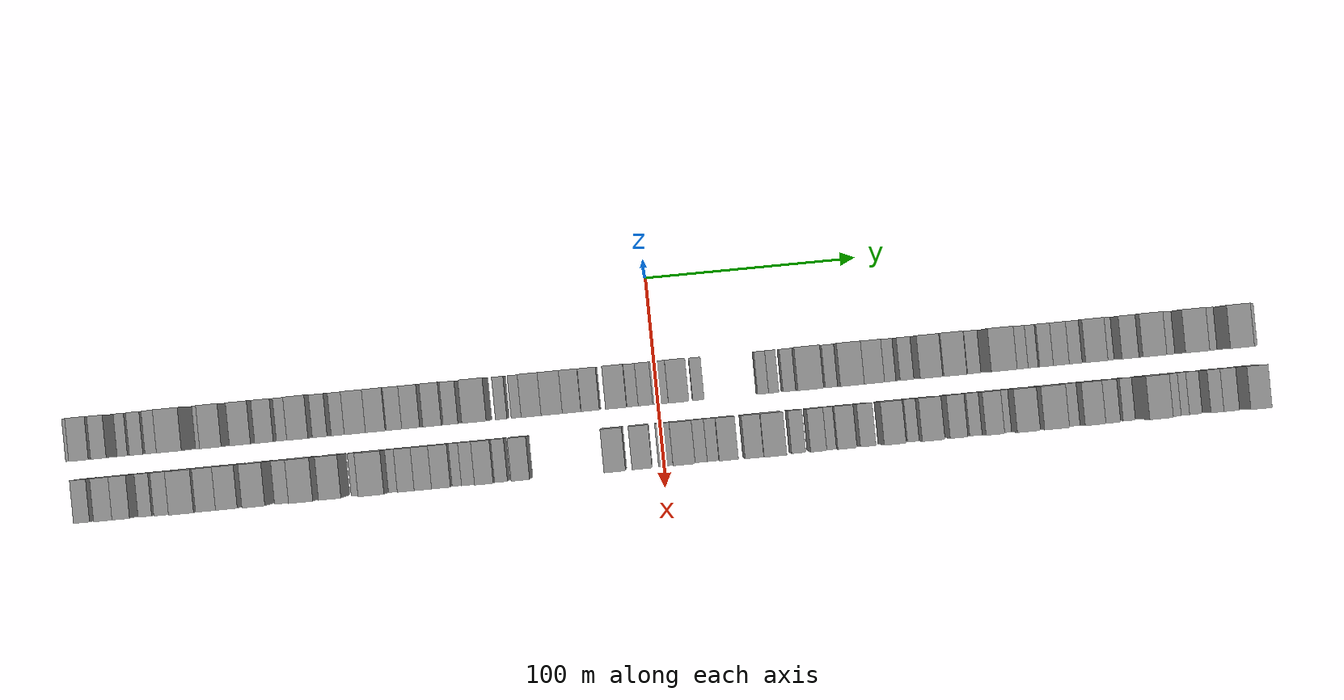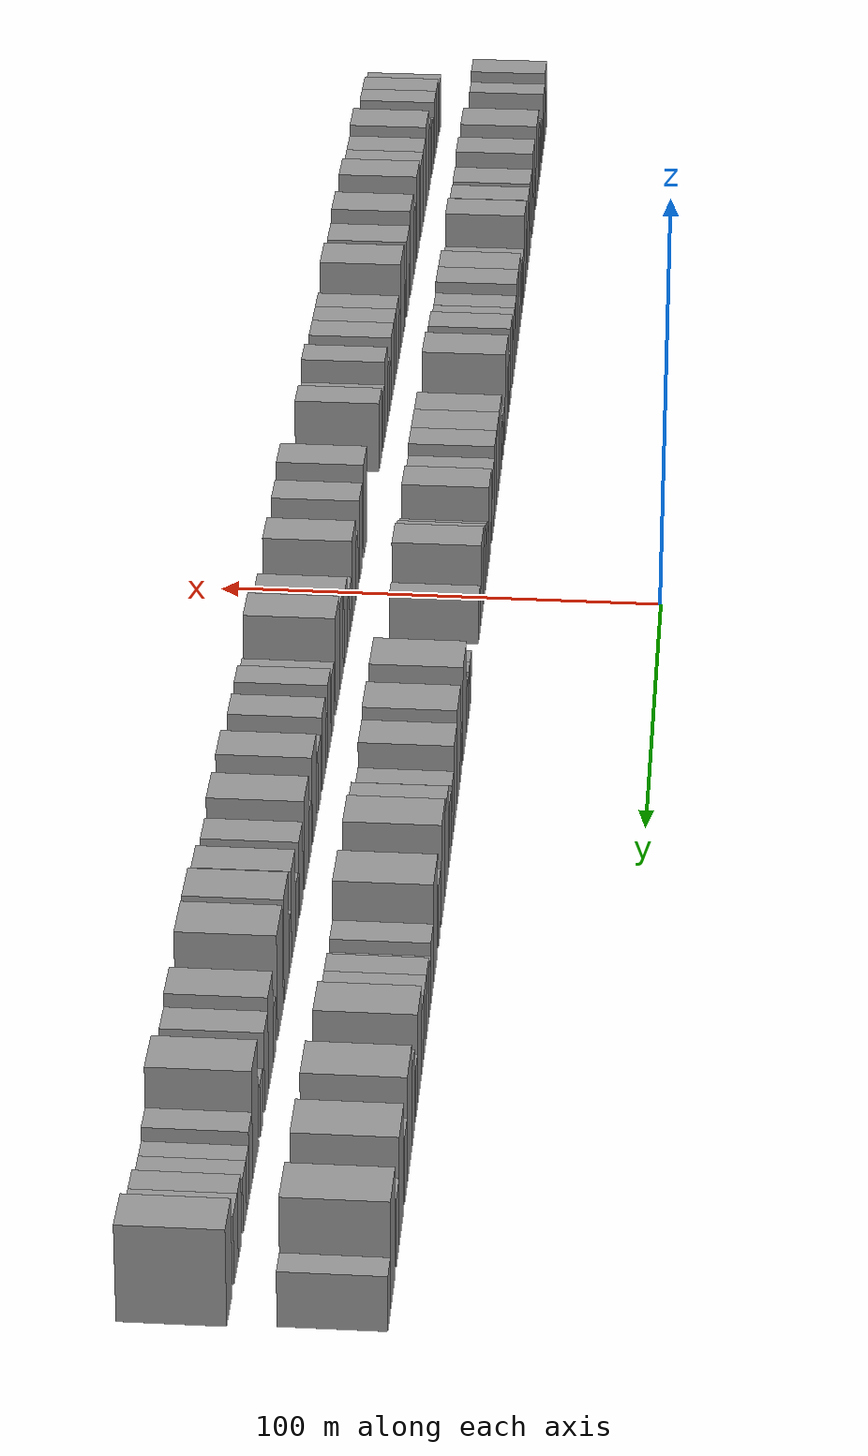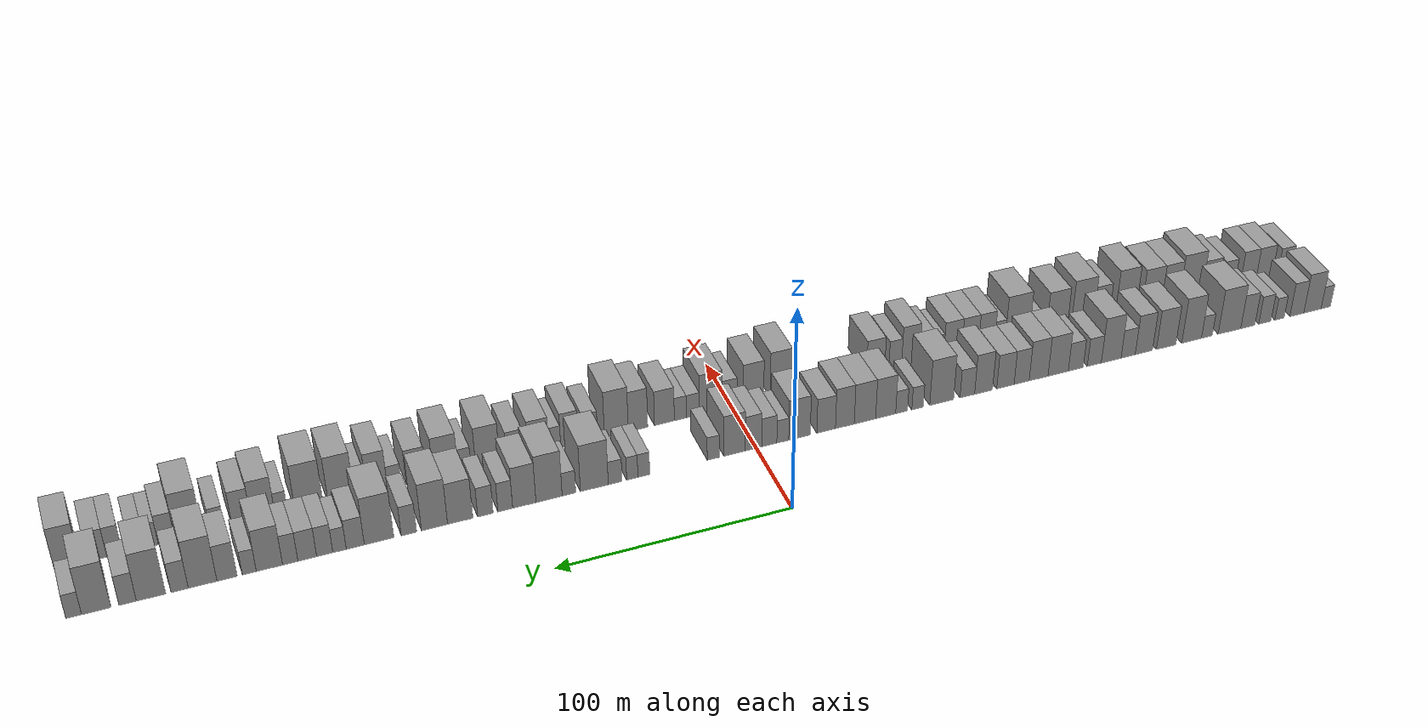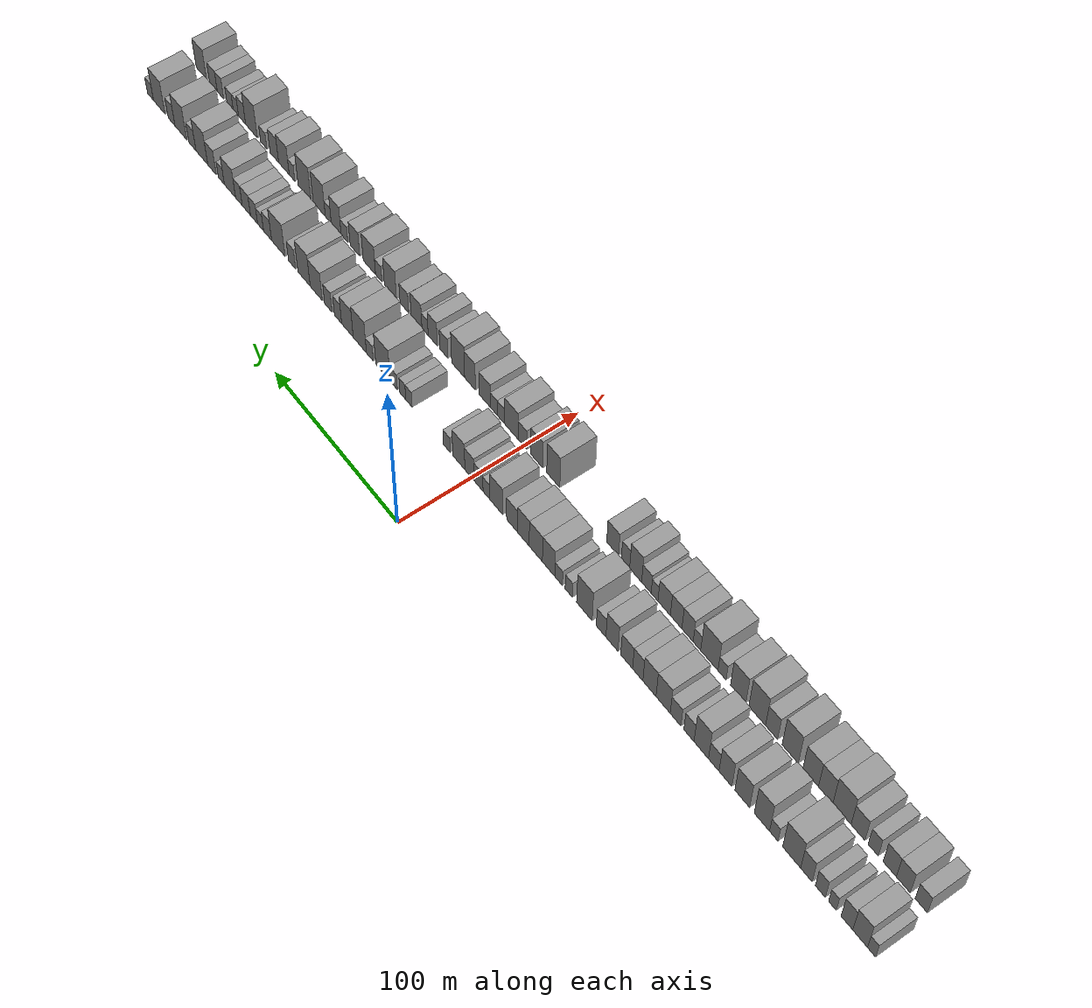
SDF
<sdf version="1.6">
 <world name="default">
  <scene>
   <sky><clouds><speed>12</speed></clouds></sky>
   <ambient>0.4 0.4 0.4 1</ambient>
   <background>0.7 0.7 0.7 1</background>
   <shadows>1</shadows>
  </scene>
  <gravity>0 0 -9.8066</gravity>
  <magnetic_field>6e-06 2.3e-05 -4.2e-05</magnetic_field>
  <physics default="0" name="default_physics" type="ode">
   <ode>
    <solver>
     <type>quick</type>
     <iters>10</iters>
     <sor>1.0</sor>
     <use_dynamic_moi_rescaling>0</use_dynamic_moi_rescaling>
    </solver>
    <constraints>
     <cfm>0</cfm>
     <erp>0.2</erp>
     <contact_max_correcting_vel>100</contact_max_correcting_vel>
     <contact_surface_layer>0.001</contact_surface_layer>
    </constraints>
   </ode>
   <max_step_size>0.004</max_step_size>
   <real_time_factor>1</real_time_factor>
   <real_time_update_rate>250</real_time_update_rate>
  </physics>
  <light name="sun" type="directional">
   <pose>0 0 10 0 0 0</pose>
   <diffuse>0.8 0.8 0.8 1</diffuse>
   <specular>0.2 0.2 0.2 1</specular>
   <attenuation>
    <range>1000</range>
    <constant>0.9</constant>
    <linear>0.01</linear>
    <quadratic>0.001</quadratic>
   </attenuation>
   <direction>-0.5 0.1 -0.9</direction>
  </light>
  <model name="building_1">
   <static>1</static>
   <pose>50.0000 -275.5481 0 0.000000 0.000000 0.000000</pose>
   <link name="link">
    <pose>0 0 6.00 0 0 0</pose>
    <collision name="collision"><geometry><box><size>20.0000 4.9038 12.0000</size></box></geometry></collision>
    <visual name="visual">
     <cast_shadows>0</cast_shadows>
     <geometry><box><size>20.0000 4.9038 12.0000</size></box></geometry>
     <material>
      <script>
       <uri>model://grey_wall/materials/scripts</uri>
       <uri>model://grey_wall/materials/textures</uri>
       <name>vrc/grey_wall</name>
      </script>
     </material>
    </visual>
   </link>
  </model>
  <model name="building_2">
   <static>1</static>
   <pose>50.0000 -268.5620 0 0.000000 0.000000 0.000000</pose>
   <link name="link">
    <pose>0 0 10.50 0 0 0</pose>
    <collision name="collision"><geometry><box><size>20.0000 9.0684 21.0000</size></box></geometry></collision>
    <visual name="visual">
     <cast_shadows>0</cast_shadows>
     <geometry><box><size>20.0000 9.0684 21.0000</size></box></geometry>
     <material>
      <script>
       <uri>model://grey_wall/materials/scripts</uri>
       <uri>model://grey_wall/materials/textures</uri>
       <name>vrc/grey_wall</name>
      </script>
     </material>
    </visual>
   </link>
  </model>
  <model name="building_3">
   <static>1</static>
   <pose>50.0000 -260.4158 0 0.000000 0.000000 0.000000</pose>
   <link name="link">
    <pose>0 0 9.00 0 0 0</pose>
    <collision name="collision"><geometry><box><size>20.0000 7.2238 18.0000</size></box></geometry></collision>
    <visual name="visual">
     <cast_shadows>0</cast_shadows>
     <geometry><box><size>20.0000 7.2238 18.0000</size></box></geometry>
     <material>
      <script>
       <uri>model://grey_wall/materials/scripts</uri>
       <uri>model://grey_wall/materials/textures</uri>
       <name>vrc/grey_wall</name>
      </script>
     </material>
    </visual>
   </link>
  </model>
  <model name="building_4">
   <static>1</static>
   <pose>50.0000 -251.4031 0 0.000000 0.000000 0.000000</pose>
   <link name="link">
    <pose>0 0 6.00 0 0 0</pose>
    <collision name="collision"><geometry><box><size>20.0000 4.8017 12.0000</size></box></geometry></collision>
    <visual name="visual">
     <cast_shadows>0</cast_shadows>
     <geometry><box><size>20.0000 4.8017 12.0000</size></box></geometry>
     <material>
      <script>
       <uri>model://grey_wall/materials/scripts</uri>
       <uri>model://grey_wall/materials/textures</uri>
       <name>vrc/grey_wall</name>
      </script>
     </material>
    </visual>
   </link>
  </model>
  <model name="building_5">
   <static>1</static>
   <pose>50.0000 -243.8589 0 0.000000 0.000000 0.000000</pose>
   <link name="link">
    <pose>0 0 7.50 0 0 0</pose>
    <collision name="collision"><geometry><box><size>20.0000 6.2866 15.0000</size></box></geometry></collision>
    <visual name="visual">
     <cast_shadows>0</cast_shadows>
     <geometry><box><size>20.0000 6.2866 15.0000</size></box></geometry>
     <material>
      <script>
       <uri>model://grey_wall/materials/scripts</uri>
       <uri>model://grey_wall/materials/textures</uri>
       <name>vrc/grey_wall</name>
      </script>
     </material>
    </visual>
   </link>
  </model>
  <model name="building_6">
   <static>1</static>
   <pose>50.0000 -235.0835 0 0.000000 0.000000 0.000000</pose>
   <link name="link">
    <pose>0 0 9.00 0 0 0</pose>
    <collision name="collision"><geometry><box><size>20.0000 7.2641 18.0000</size></box></geometry></collision>
    <visual name="visual">
     <cast_shadows>0</cast_shadows>
     <geometry><box><size>20.0000 7.2641 18.0000</size></box></geometry>
     <material>
      <script>
       <uri>model://grey_wall/materials/scripts</uri>
       <uri>model://grey_wall/materials/textures</uri>
       <name>vrc/grey_wall</name>
      </script>
     </material>
    </visual>
   </link>
  </model>
  <model name="building_7">
   <static>1</static>
   <pose>50.0000 -225.6979 0 0.000000 0.000000 0.000000</pose>
   <link name="link">
    <pose>0 0 12.00 0 0 0</pose>
    <collision name="collision"><geometry><box><size>20.0000 11.5071 24.0000</size></box></geometry></collision>
    <visual name="visual">
     <cast_shadows>0</cast_shadows>
     <geometry><box><size>20.0000 11.5071 24.0000</size></box></geometry>
     <material>
      <script>
       <uri>model://grey_wall/materials/scripts</uri>
       <uri>model://grey_wall/materials/textures</uri>
       <name>vrc/grey_wall</name>
      </script>
     </material>
    </visual>
   </link>
  </model>
  <model name="building_8">
   <static>1</static>
   <pose>50.0000 -214.2070 0 0.000000 0.000000 0.000000</pose>
   <link name="link">
    <pose>0 0 6.00 0 0 0</pose>
    <collision name="collision"><geometry><box><size>20.0000 5.4747 12.0000</size></box></geometry></collision>
    <visual name="visual">
     <cast_shadows>0</cast_shadows>
     <geometry><box><size>20.0000 5.4747 12.0000</size></box></geometry>
     <material>
      <script>
       <uri>model://grey_wall/materials/scripts</uri>
       <uri>model://grey_wall/materials/textures</uri>
       <name>vrc/grey_wall</name>
      </script>
     </material>
    </visual>
   </link>
  </model>
  <model name="building_9">
   <static>1</static>
   <pose>50.0000 -206.5053 0 0.000000 0.000000 0.000000</pose>
   <link name="link">
    <pose>0 0 12.00 0 0 0</pose>
    <collision name="collision"><geometry><box><size>20.0000 9.9287 24.0000</size></box></geometry></collision>
    <visual name="visual">
     <cast_shadows>0</cast_shadows>
     <geometry><box><size>20.0000 9.9287 24.0000</size></box></geometry>
     <material>
      <script>
       <uri>model://grey_wall/materials/scripts</uri>
       <uri>model://grey_wall/materials/textures</uri>
       <name>vrc/grey_wall</name>
      </script>
     </material>
    </visual>
   </link>
  </model>
  <model name="building_10">
   <static>1</static>
   <pose>50.0000 -193.6830 0 0.000000 0.000000 0.000000</pose>
   <link name="link">
    <pose>0 0 10.50 0 0 0</pose>
    <collision name="collision"><geometry><box><size>20.0000 9.7158 21.0000</size></box></geometry></collision>
    <visual name="visual">
     <cast_shadows>0</cast_shadows>
     <geometry><box><size>20.0000 9.7158 21.0000</size></box></geometry>
     <material>
      <script>
       <uri>model://grey_wall/materials/scripts</uri>
       <uri>model://grey_wall/materials/textures</uri>
       <name>vrc/grey_wall</name>
      </script>
     </material>
    </visual>
   </link>
  </model>
  <model name="building_11">
   <static>1</static>
   <pose>50.0000 -182.5326 0 0.000000 0.000000 0.000000</pose>
   <link name="link">
    <pose>0 0 10.50 0 0 0</pose>
    <collision name="collision"><geometry><box><size>20.0000 8.5851 21.0000</size></box></geometry></collision>
    <visual name="visual">
     <cast_shadows>0</cast_shadows>
     <geometry><box><size>20.0000 8.5851 21.0000</size></box></geometry>
     <material>
      <script>
       <uri>model://grey_wall/materials/scripts</uri>
       <uri>model://grey_wall/materials/textures</uri>
       <name>vrc/grey_wall</name>
      </script>
     </material>
    </visual>
   </link>
  </model>
  <model name="building_12">
   <static>1</static>
   <pose>50.0000 -174.7368 0 0.000000 0.000000 0.000000</pose>
   <link name="link">
    <pose>0 0 7.50 0 0 0</pose>
    <collision name="collision"><geometry><box><size>20.0000 7.0065 15.0000</size></box></geometry></collision>
    <visual name="visual">
     <cast_shadows>0</cast_shadows>
     <geometry><box><size>20.0000 7.0065 15.0000</size></box></geometry>
     <material>
      <script>
       <uri>model://grey_wall/materials/scripts</uri>
       <uri>model://grey_wall/materials/textures</uri>
       <name>vrc/grey_wall</name>
      </script>
     </material>
    </visual>
   </link>
  </model>
  <model name="building_13">
   <static>1</static>
   <pose>50.0000 -166.3466 0 0.000000 0.000000 0.000000</pose>
   <link name="link">
    <pose>0 0 12.00 0 0 0</pose>
    <collision name="collision"><geometry><box><size>20.0000 9.7737 24.0000</size></box></geometry></collision>
    <visual name="visual">
     <cast_shadows>0</cast_shadows>
     <geometry><box><size>20.0000 9.7737 24.0000</size></box></geometry>
     <material>
      <script>
       <uri>model://grey_wall/materials/scripts</uri>
       <uri>model://grey_wall/materials/textures</uri>
       <name>vrc/grey_wall</name>
      </script>
     </material>
    </visual>
   </link>
  </model>
  <model name="building_14">
   <static>1</static>
   <pose>50.0000 -158.0214 0 0.000000 0.000000 0.000000</pose>
   <link name="link">
    <pose>0 0 7.50 0 0 0</pose>
    <collision name="collision"><geometry><box><size>20.0000 6.8768 15.0000</size></box></geometry></collision>
    <visual name="visual">
     <cast_shadows>0</cast_shadows>
     <geometry><box><size>20.0000 6.8768 15.0000</size></box></geometry>
     <material>
      <script>
       <uri>model://grey_wall/materials/scripts</uri>
       <uri>model://grey_wall/materials/textures</uri>
       <name>vrc/grey_wall</name>
      </script>
     </material>
    </visual>
   </link>
  </model>
  <model name="building_15">
   <static>1</static>
   <pose>50.0000 -148.9271 0 0.000000 0.000000 0.000000</pose>
   <link name="link">
    <pose>0 0 7.50 0 0 0</pose>
    <collision name="collision"><geometry><box><size>20.0000 7.3119 15.0000</size></box></geometry></collision>
    <visual name="visual">
     <cast_shadows>0</cast_shadows>
     <geometry><box><size>20.0000 7.3119 15.0000</size></box></geometry>
     <material>
      <script>
       <uri>model://grey_wall/materials/scripts</uri>
       <uri>model://grey_wall/materials/textures</uri>
       <name>vrc/grey_wall</name>
      </script>
     </material>
    </visual>
   </link>
  </model>
  <model name="building_16">
   <static>1</static>
   <pose>50.0000 -140.3689 0 0.000000 0.000000 0.000000</pose>
   <link name="link">
    <pose>0 0 10.50 0 0 0</pose>
    <collision name="collision"><geometry><box><size>20.0000 9.8044 21.0000</size></box></geometry></collision>
    <visual name="visual">
     <cast_shadows>0</cast_shadows>
     <geometry><box><size>20.0000 9.8044 21.0000</size></box></geometry>
     <material>
      <script>
       <uri>model://grey_wall/materials/scripts</uri>
       <uri>model://grey_wall/materials/textures</uri>
       <name>vrc/grey_wall</name>
      </script>
     </material>
    </visual>
   </link>
  </model>
  <model name="building_17">
   <static>1</static>
   <pose>50.0000 -130.9030 0 0.000000 0.000000 0.000000</pose>
   <link name="link">
    <pose>0 0 10.50 0 0 0</pose>
    <collision name="collision"><geometry><box><size>20.0000 9.1274 21.0000</size></box></geometry></collision>
    <visual name="visual">
     <cast_shadows>0</cast_shadows>
     <geometry><box><size>20.0000 9.1274 21.0000</size></box></geometry>
     <material>
      <script>
       <uri>model://grey_wall/materials/scripts</uri>
       <uri>model://grey_wall/materials/textures</uri>
       <name>vrc/grey_wall</name>
      </script>
     </material>
    </visual>
   </link>
  </model>
  <model name="building_18">
   <static>1</static>
   <pose>50.0000 -122.7302 0 0.000000 0.000000 0.000000</pose>
   <link name="link">
    <pose>0 0 9.00 0 0 0</pose>
    <collision name="collision"><geometry><box><size>20.0000 7.2182 18.0000</size></box></geometry></collision>
    <visual name="visual">
     <cast_shadows>0</cast_shadows>
     <geometry><box><size>20.0000 7.2182 18.0000</size></box></geometry>
     <material>
      <script>
       <uri>model://grey_wall/materials/scripts</uri>
       <uri>model://grey_wall/materials/textures</uri>
       <name>vrc/grey_wall</name>
      </script>
     </material>
    </visual>
   </link>
  </model>
  <model name="building_19">
   <static>1</static>
   <pose>50.0000 -114.9601 0 0.000000 0.000000 0.000000</pose>
   <link name="link">
    <pose>0 0 9.00 0 0 0</pose>
    <collision name="collision"><geometry><box><size>20.0000 8.3221 18.0000</size></box></geometry></collision>
    <visual name="visual">
     <cast_shadows>0</cast_shadows>
     <geometry><box><size>20.0000 8.3221 18.0000</size></box></geometry>
     <material>
      <script>
       <uri>model://grey_wall/materials/scripts</uri>
       <uri>model://grey_wall/materials/textures</uri>
       <name>vrc/grey_wall</name>
      </script>
     </material>
    </visual>
   </link>
  </model>
  <model name="building_20">
   <static>1</static>
   <pose>50.0000 -104.5384 0 0.000000 0.000000 0.000000</pose>
   <link name="link">
    <pose>0 0 10.50 0 0 0</pose>
    <collision name="collision"><geometry><box><size>20.0000 8.5211 21.0000</size></box></geometry></collision>
    <visual name="visual">
     <cast_shadows>0</cast_shadows>
     <geometry><box><size>20.0000 8.5211 21.0000</size></box></geometry>
     <material>
      <script>
       <uri>model://grey_wall/materials/scripts</uri>
       <uri>model://grey_wall/materials/textures</uri>
       <name>vrc/grey_wall</name>
      </script>
     </material>
    </visual>
   </link>
  </model>
  <model name="building_21">
   <static>1</static>
   <pose>50.0000 -96.8199 0 0.000000 0.000000 0.000000</pose>
   <link name="link">
    <pose>0 0 7.50 0 0 0</pose>
    <collision name="collision"><geometry><box><size>20.0000 6.9159 15.0000</size></box></geometry></collision>
    <visual name="visual">
     <cast_shadows>0</cast_shadows>
     <geometry><box><size>20.0000 6.9159 15.0000</size></box></geometry>
     <material>
      <script>
       <uri>model://grey_wall/materials/scripts</uri>
       <uri>model://grey_wall/materials/textures</uri>
       <name>vrc/grey_wall</name>
      </script>
     </material>
    </visual>
   </link>
  </model>
  <model name="building_22">
   <static>1</static>
   <pose>50.0000 -84.7452 0 0.000000 0.000000 0.000000</pose>
   <link name="link">
    <pose>0 0 12.00 0 0 0</pose>
    <collision name="collision"><geometry><box><size>20.0000 11.2335 24.0000</size></box></geometry></collision>
    <visual name="visual">
     <cast_shadows>0</cast_shadows>
     <geometry><box><size>20.0000 11.2335 24.0000</size></box></geometry>
     <material>
      <script>
       <uri>model://grey_wall/materials/scripts</uri>
       <uri>model://grey_wall/materials/textures</uri>
       <name>vrc/grey_wall</name>
      </script>
     </material>
    </visual>
   </link>
  </model>
  <model name="building_23">
   <static>1</static>
   <pose>50.0000 -73.4463 0 0.000000 0.000000 0.000000</pose>
   <link name="link">
    <pose>0 0 6.00 0 0 0</pose>
    <collision name="collision"><geometry><box><size>20.0000 5.3645 12.0000</size></box></geometry></collision>
    <visual name="visual">
     <cast_shadows>0</cast_shadows>
     <geometry><box><size>20.0000 5.3645 12.0000</size></box></geometry>
     <material>
      <script>
       <uri>model://grey_wall/materials/scripts</uri>
       <uri>model://grey_wall/materials/textures</uri>
       <name>vrc/grey_wall</name>
      </script>
     </material>
    </visual>
   </link>
  </model>
  <model name="building_24">
   <static>1</static>
   <pose>50.0000 -65.9950 0 0.000000 0.000000 0.000000</pose>
   <link name="link">
    <pose>0 0 6.00 0 0 0</pose>
    <collision name="collision"><geometry><box><size>20.0000 5.5381 12.0000</size></box></geometry></collision>
    <visual name="visual">
     <cast_shadows>0</cast_shadows>
     <geometry><box><size>20.0000 5.5381 12.0000</size></box></geometry>
     <material>
      <script>
       <uri>model://grey_wall/materials/scripts</uri>
       <uri>model://grey_wall/materials/textures</uri>
       <name>vrc/grey_wall</name>
      </script>
     </material>
    </visual>
   </link>
  </model>
  <model name="building_25">
   <static>1</static>
   <pose>50.0000 -58.6003 0 0.000000 0.000000 0.000000</pose>
   <link name="link">
    <pose>0 0 10.50 0 0 0</pose>
    <collision name="collision"><geometry><box><size>20.0000 9.2512 21.0000</size></box></geometry></collision>
    <visual name="visual">
     <cast_shadows>0</cast_shadows>
     <geometry><box><size>20.0000 9.2512 21.0000</size></box></geometry>
     <material>
      <script>
       <uri>model://grey_wall/materials/scripts</uri>
       <uri>model://grey_wall/materials/textures</uri>
       <name>vrc/grey_wall</name>
      </script>
     </material>
    </visual>
   </link>
  </model>
  <model name="building_26">
   <static>1</static>
   <pose>50.0000 -49.0487 0 0.000000 0.000000 0.000000</pose>
   <link name="link">
    <pose>0 0 10.50 0 0 0</pose>
    <collision name="collision"><geometry><box><size>20.0000 9.8520 21.0000</size></box></geometry></collision>
    <visual name="visual">
     <cast_shadows>0</cast_shadows>
     <geometry><box><size>20.0000 9.8520 21.0000</size></box></geometry>
     <material>
      <script>
       <uri>model://grey_wall/materials/scripts</uri>
       <uri>model://grey_wall/materials/textures</uri>
       <name>vrc/grey_wall</name>
      </script>
     </material>
    </visual>
   </link>
  </model>
  <model name="building_27">
   <static>1</static>
   <pose>50.0000 -39.8249 0 0.000000 0.000000 0.000000</pose>
   <link name="link">
    <pose>0 0 10.50 0 0 0</pose>
    <collision name="collision"><geometry><box><size>20.0000 8.5956 21.0000</size></box></geometry></collision>
    <visual name="visual">
     <cast_shadows>0</cast_shadows>
     <geometry><box><size>20.0000 8.5956 21.0000</size></box></geometry>
     <material>
      <script>
       <uri>model://grey_wall/materials/scripts</uri>
       <uri>model://grey_wall/materials/textures</uri>
       <name>vrc/grey_wall</name>
      </script>
     </material>
    </visual>
   </link>
  </model>
  <model name="building_28">
   <static>1</static>
   <pose>50.0000 -31.3022 0 0.000000 0.000000 0.000000</pose>
   <link name="link">
    <pose>0 0 9.00 0 0 0</pose>
    <collision name="collision"><geometry><box><size>20.0000 8.4498 18.0000</size></box></geometry></collision>
    <visual name="visual">
     <cast_shadows>0</cast_shadows>
     <geometry><box><size>20.0000 8.4498 18.0000</size></box></geometry>
     <material>
      <script>
       <uri>model://grey_wall/materials/scripts</uri>
       <uri>model://grey_wall/materials/textures</uri>
       <name>vrc/grey_wall</name>
      </script>
     </material>
    </visual>
   </link>
  </model>
  <model name="building_29">
   <static>1</static>
   <pose>50.0000 -19.2158 0 0.000000 0.000000 0.000000</pose>
   <link name="link">
    <pose>0 0 10.50 0 0 0</pose>
    <collision name="collision"><geometry><box><size>20.0000 9.7230 21.0000</size></box></geometry></collision>
    <visual name="visual">
     <cast_shadows>0</cast_shadows>
     <geometry><box><size>20.0000 9.7230 21.0000</size></box></geometry>
     <material>
      <script>
       <uri>model://grey_wall/materials/scripts</uri>
       <uri>model://grey_wall/materials/textures</uri>
       <name>vrc/grey_wall</name>
      </script>
     </material>
    </visual>
   </link>
  </model>
  <model name="building_30">
   <static>1</static>
   <pose>50.0000 -11.6826 0 0.000000 0.000000 0.000000</pose>
   <link name="link">
    <pose>0 0 6.00 0 0 0</pose>
    <collision name="collision"><geometry><box><size>20.0000 5.3433 12.0000</size></box></geometry></collision>
    <visual name="visual">
     <cast_shadows>0</cast_shadows>
     <geometry><box><size>20.0000 5.3433 12.0000</size></box></geometry>
     <material>
      <script>
       <uri>model://grey_wall/materials/scripts</uri>
       <uri>model://grey_wall/materials/textures</uri>
       <name>vrc/grey_wall</name>
      </script>
     </material>
    </visual>
   </link>
  </model>
  <model name="building_31">
   <static>1</static>
   <pose>50.0000 -5.6127 0 0.000000 0.000000 0.000000</pose>
   <link name="link">
    <pose>0 0 7.50 0 0 0</pose>
    <collision name="collision"><geometry><box><size>20.0000 6.7966 15.0000</size></box></geometry></collision>
    <visual name="visual">
     <cast_shadows>0</cast_shadows>
     <geometry><box><size>20.0000 6.7966 15.0000</size></box></geometry>
     <material>
      <script>
       <uri>model://grey_wall/materials/scripts</uri>
       <uri>model://grey_wall/materials/textures</uri>
       <name>vrc/grey_wall</name>
      </script>
     </material>
    </visual>
   </link>
  </model>
  <model name="building_32">
   <static>1</static>
   <pose>50.0000 1.4330 0 0.000000 0.000000 0.000000</pose>
   <link name="link">
    <pose>0 0 9.00 0 0 0</pose>
    <collision name="collision"><geometry><box><size>20.0000 7.2947 18.0000</size></box></geometry></collision>
    <visual name="visual">
     <cast_shadows>0</cast_shadows>
     <geometry><box><size>20.0000 7.2947 18.0000</size></box></geometry>
     <material>
      <script>
       <uri>model://grey_wall/materials/scripts</uri>
       <uri>model://grey_wall/materials/textures</uri>
       <name>vrc/grey_wall</name>
      </script>
     </material>
    </visual>
   </link>
  </model>
  <model name="building_33">
   <static>1</static>
   <pose>50.0000 9.8166 0 0.000000 0.000000 0.000000</pose>
   <link name="link">
    <pose>0 0 10.50 0 0 0</pose>
    <collision name="collision"><geometry><box><size>20.0000 9.4724 21.0000</size></box></geometry></collision>
    <visual name="visual">
     <cast_shadows>0</cast_shadows>
     <geometry><box><size>20.0000 9.4724 21.0000</size></box></geometry>
     <material>
      <script>
       <uri>model://grey_wall/materials/scripts</uri>
       <uri>model://grey_wall/materials/textures</uri>
       <name>vrc/grey_wall</name>
      </script>
     </material>
    </visual>
   </link>
  </model>
  <model name="building_34">
   <static>1</static>
   <pose>50.0000 19.2327 0 0.000000 0.000000 0.000000</pose>
   <link name="link">
    <pose>0 0 6.00 0 0 0</pose>
    <collision name="collision"><geometry><box><size>20.0000 5.3598 12.0000</size></box></geometry></collision>
    <visual name="visual">
     <cast_shadows>0</cast_shadows>
     <geometry><box><size>20.0000 5.3598 12.0000</size></box></geometry>
     <material>
      <script>
       <uri>model://grey_wall/materials/scripts</uri>
       <uri>model://grey_wall/materials/textures</uri>
       <name>vrc/grey_wall</name>
      </script>
     </material>
    </visual>
   </link>
  </model>
  <model name="building_35">
   <static>1</static>
   <pose>50.0000 49.6123 0 0.000000 0.000000 0.000000</pose>
   <link name="link">
    <pose>0 0 6.00 0 0 0</pose>
    <collision name="collision"><geometry><box><size>20.0000 5.1332 12.0000</size></box></geometry></collision>
    <visual name="visual">
     <cast_shadows>0</cast_shadows>
     <geometry><box><size>20.0000 5.1332 12.0000</size></box></geometry>
     <material>
      <script>
       <uri>model://grey_wall/materials/scripts</uri>
       <uri>model://grey_wall/materials/textures</uri>
       <name>vrc/grey_wall</name>
      </script>
     </material>
    </visual>
   </link>
  </model>
  <model name="building_36">
   <static>1</static>
   <pose>50.0000 54.5868 0 0.000000 0.000000 0.000000</pose>
   <link name="link">
    <pose>0 0 6.00 0 0 0</pose>
    <collision name="collision"><geometry><box><size>20.0000 4.8158 12.0000</size></box></geometry></collision>
    <visual name="visual">
     <cast_shadows>0</cast_shadows>
     <geometry><box><size>20.0000 4.8158 12.0000</size></box></geometry>
     <material>
      <script>
       <uri>model://grey_wall/materials/scripts</uri>
       <uri>model://grey_wall/materials/textures</uri>
       <name>vrc/grey_wall</name>
      </script>
     </material>
    </visual>
   </link>
  </model>
  <model name="building_37">
   <static>1</static>
   <pose>50.0000 61.9565 0 0.000000 0.000000 0.000000</pose>
   <link name="link">
    <pose>0 0 6.00 0 0 0</pose>
    <collision name="collision"><geometry><box><size>20.0000 5.9236 12.0000</size></box></geometry></collision>
    <visual name="visual">
     <cast_shadows>0</cast_shadows>
     <geometry><box><size>20.0000 5.9236 12.0000</size></box></geometry>
     <material>
      <script>
       <uri>model://grey_wall/materials/scripts</uri>
       <uri>model://grey_wall/materials/textures</uri>
       <name>vrc/grey_wall</name>
      </script>
     </material>
    </visual>
   </link>
  </model>
  <model name="building_38">
   <static>1</static>
   <pose>50.0000 70.8551 0 0.000000 0.000000 0.000000</pose>
   <link name="link">
    <pose>0 0 12.00 0 0 0</pose>
    <collision name="collision"><geometry><box><size>20.0000 11.8737 24.0000</size></box></geometry></collision>
    <visual name="visual">
     <cast_shadows>0</cast_shadows>
     <geometry><box><size>20.0000 11.8737 24.0000</size></box></geometry>
     <material>
      <script>
       <uri>model://grey_wall/materials/scripts</uri>
       <uri>model://grey_wall/materials/textures</uri>
       <name>vrc/grey_wall</name>
      </script>
     </material>
    </visual>
   </link>
  </model>
  <model name="building_39">
   <static>1</static>
   <pose>50.0000 81.6715 0 0.000000 0.000000 0.000000</pose>
   <link name="link">
    <pose>0 0 6.00 0 0 0</pose>
    <collision name="collision"><geometry><box><size>20.0000 5.7592 12.0000</size></box></geometry></collision>
    <visual name="visual">
     <cast_shadows>0</cast_shadows>
     <geometry><box><size>20.0000 5.7592 12.0000</size></box></geometry>
     <material>
      <script>
       <uri>model://grey_wall/materials/scripts</uri>
       <uri>model://grey_wall/materials/textures</uri>
       <name>vrc/grey_wall</name>
      </script>
     </material>
    </visual>
   </link>
  </model>
  <model name="building_40">
   <static>1</static>
   <pose>50.0000 90.0841 0 0.000000 0.000000 0.000000</pose>
   <link name="link">
    <pose>0 0 12.00 0 0 0</pose>
    <collision name="collision"><geometry><box><size>20.0000 11.0659 24.0000</size></box></geometry></collision>
    <visual name="visual">
     <cast_shadows>0</cast_shadows>
     <geometry><box><size>20.0000 11.0659 24.0000</size></box></geometry>
     <material>
      <script>
       <uri>model://grey_wall/materials/scripts</uri>
       <uri>model://grey_wall/materials/textures</uri>
       <name>vrc/grey_wall</name>
      </script>
     </material>
    </visual>
   </link>
  </model>
  <model name="building_41">
   <static>1</static>
   <pose>50.0000 100.4950 0 0.000000 0.000000 0.000000</pose>
   <link name="link">
    <pose>0 0 10.50 0 0 0</pose>
    <collision name="collision"><geometry><box><size>20.0000 9.7560 21.0000</size></box></geometry></collision>
    <visual name="visual">
     <cast_shadows>0</cast_shadows>
     <geometry><box><size>20.0000 9.7560 21.0000</size></box></geometry>
     <material>
      <script>
       <uri>model://grey_wall/materials/scripts</uri>
       <uri>model://grey_wall/materials/textures</uri>
       <name>vrc/grey_wall</name>
      </script>
     </material>
    </visual>
   </link>
  </model>
  <model name="building_42">
   <static>1</static>
   <pose>50.0000 108.4439 0 0.000000 0.000000 0.000000</pose>
   <link name="link">
    <pose>0 0 7.50 0 0 0</pose>
    <collision name="collision"><geometry><box><size>20.0000 6.1417 15.0000</size></box></geometry></collision>
    <visual name="visual">
     <cast_shadows>0</cast_shadows>
     <geometry><box><size>20.0000 6.1417 15.0000</size></box></geometry>
     <material>
      <script>
       <uri>model://grey_wall/materials/scripts</uri>
       <uri>model://grey_wall/materials/textures</uri>
       <name>vrc/grey_wall</name>
      </script>
     </material>
    </visual>
   </link>
  </model>
  <model name="building_43">
   <static>1</static>
   <pose>50.0000 116.7154 0 0.000000 0.000000 0.000000</pose>
   <link name="link">
    <pose>0 0 7.50 0 0 0</pose>
    <collision name="collision"><geometry><box><size>20.0000 6.4013 15.0000</size></box></geometry></collision>
    <visual name="visual">
     <cast_shadows>0</cast_shadows>
     <geometry><box><size>20.0000 6.4013 15.0000</size></box></geometry>
     <material>
      <script>
       <uri>model://grey_wall/materials/scripts</uri>
       <uri>model://grey_wall/materials/textures</uri>
       <name>vrc/grey_wall</name>
      </script>
     </material>
    </visual>
   </link>
  </model>
  <model name="building_44">
   <static>1</static>
   <pose>50.0000 127.1269 0 0.000000 0.000000 0.000000</pose>
   <link name="link">
    <pose>0 0 10.50 0 0 0</pose>
    <collision name="collision"><geometry><box><size>20.0000 10.4218 21.0000</size></box></geometry></collision>
    <visual name="visual">
     <cast_shadows>0</cast_shadows>
     <geometry><box><size>20.0000 10.4218 21.0000</size></box></geometry>
     <material>
      <script>
       <uri>model://grey_wall/materials/scripts</uri>
       <uri>model://grey_wall/materials/textures</uri>
       <name>vrc/grey_wall</name>
      </script>
     </material>
    </visual>
   </link>
  </model>
  <model name="building_45">
   <static>1</static>
   <pose>50.0000 137.6844 0 0.000000 0.000000 0.000000</pose>
   <link name="link">
    <pose>0 0 12.00 0 0 0</pose>
    <collision name="collision"><geometry><box><size>20.0000 10.6931 24.0000</size></box></geometry></collision>
    <visual name="visual">
     <cast_shadows>0</cast_shadows>
     <geometry><box><size>20.0000 10.6931 24.0000</size></box></geometry>
     <material>
      <script>
       <uri>model://grey_wall/materials/scripts</uri>
       <uri>model://grey_wall/materials/textures</uri>
       <name>vrc/grey_wall</name>
      </script>
     </material>
    </visual>
   </link>
  </model>
  <model name="building_46">
   <static>1</static>
   <pose>50.0000 148.1507 0 0.000000 0.000000 0.000000</pose>
   <link name="link">
    <pose>0 0 7.50 0 0 0</pose>
    <collision name="collision"><geometry><box><size>20.0000 6.2395 15.0000</size></box></geometry></collision>
    <visual name="visual">
     <cast_shadows>0</cast_shadows>
     <geometry><box><size>20.0000 6.2395 15.0000</size></box></geometry>
     <material>
      <script>
       <uri>model://grey_wall/materials/scripts</uri>
       <uri>model://grey_wall/materials/textures</uri>
       <name>vrc/grey_wall</name>
      </script>
     </material>
    </visual>
   </link>
  </model>
  <model name="building_47">
   <static>1</static>
   <pose>50.0000 160.2290 0 0.000000 0.000000 0.000000</pose>
   <link name="link">
    <pose>0 0 12.00 0 0 0</pose>
    <collision name="collision"><geometry><box><size>20.0000 11.9171 24.0000</size></box></geometry></collision>
    <visual name="visual">
     <cast_shadows>0</cast_shadows>
     <geometry><box><size>20.0000 11.9171 24.0000</size></box></geometry>
     <material>
      <script>
       <uri>model://grey_wall/materials/scripts</uri>
       <uri>model://grey_wall/materials/textures</uri>
       <name>vrc/grey_wall</name>
      </script>
     </material>
    </visual>
   </link>
  </model>
  <model name="building_48">
   <static>1</static>
   <pose>50.0000 169.8042 0 0.000000 0.000000 0.000000</pose>
   <link name="link">
    <pose>0 0 7.50 0 0 0</pose>
    <collision name="collision"><geometry><box><size>20.0000 7.2333 15.0000</size></box></geometry></collision>
    <visual name="visual">
     <cast_shadows>0</cast_shadows>
     <geometry><box><size>20.0000 7.2333 15.0000</size></box></geometry>
     <material>
      <script>
       <uri>model://grey_wall/materials/scripts</uri>
       <uri>model://grey_wall/materials/textures</uri>
       <name>vrc/grey_wall</name>
      </script>
     </material>
    </visual>
   </link>
  </model>
  <model name="building_49">
   <static>1</static>
   <pose>50.0000 176.1011 0 0.000000 0.000000 0.000000</pose>
   <link name="link">
    <pose>0 0 6.00 0 0 0</pose>
    <collision name="collision"><geometry><box><size>20.0000 5.3603 12.0000</size></box></geometry></collision>
    <visual name="visual">
     <cast_shadows>0</cast_shadows>
     <geometry><box><size>20.0000 5.3603 12.0000</size></box></geometry>
     <material>
      <script>
       <uri>model://grey_wall/materials/scripts</uri>
       <uri>model://grey_wall/materials/textures</uri>
       <name>vrc/grey_wall</name>
      </script>
     </material>
    </visual>
   </link>
  </model>
  <model name="building_50">
   <static>1</static>
   <pose>50.0000 181.9888 0 0.000000 0.000000 0.000000</pose>
   <link name="link">
    <pose>0 0 7.50 0 0 0</pose>
    <collision name="collision"><geometry><box><size>20.0000 6.4152 15.0000</size></box></geometry></collision>
    <visual name="visual">
     <cast_shadows>0</cast_shadows>
     <geometry><box><size>20.0000 6.4152 15.0000</size></box></geometry>
     <material>
      <script>
       <uri>model://grey_wall/materials/scripts</uri>
       <uri>model://grey_wall/materials/textures</uri>
       <name>vrc/grey_wall</name>
      </script>
     </material>
    </visual>
   </link>
  </model>
  <model name="building_51">
   <static>1</static>
   <pose>50.0000 188.9186 0 0.000000 0.000000 0.000000</pose>
   <link name="link">
    <pose>0 0 7.50 0 0 0</pose>
    <collision name="collision"><geometry><box><size>20.0000 7.4444 15.0000</size></box></geometry></collision>
    <visual name="visual">
     <cast_shadows>0</cast_shadows>
     <geometry><box><size>20.0000 7.4444 15.0000</size></box></geometry>
     <material>
      <script>
       <uri>model://grey_wall/materials/scripts</uri>
       <uri>model://grey_wall/materials/textures</uri>
       <name>vrc/grey_wall</name>
      </script>
     </material>
    </visual>
   </link>
  </model>
  <model name="building_52">
   <static>1</static>
   <pose>50.0000 195.6576 0 0.000000 0.000000 0.000000</pose>
   <link name="link">
    <pose>0 0 7.50 0 0 0</pose>
    <collision name="collision"><geometry><box><size>20.0000 6.0336 15.0000</size></box></geometry></collision>
    <visual name="visual">
     <cast_shadows>0</cast_shadows>
     <geometry><box><size>20.0000 6.0336 15.0000</size></box></geometry>
     <material>
      <script>
       <uri>model://grey_wall/materials/scripts</uri>
       <uri>model://grey_wall/materials/textures</uri>
       <name>vrc/grey_wall</name>
      </script>
     </material>
    </visual>
   </link>
  </model>
  <model name="building_53">
   <static>1</static>
   <pose>50.0000 203.8376 0 0.000000 0.000000 0.000000</pose>
   <link name="link">
    <pose>0 0 10.50 0 0 0</pose>
    <collision name="collision"><geometry><box><size>20.0000 10.3264 21.0000</size></box></geometry></collision>
    <visual name="visual">
     <cast_shadows>0</cast_shadows>
     <geometry><box><size>20.0000 10.3264 21.0000</size></box></geometry>
     <material>
      <script>
       <uri>model://grey_wall/materials/scripts</uri>
       <uri>model://grey_wall/materials/textures</uri>
       <name>vrc/grey_wall</name>
      </script>
     </material>
    </visual>
   </link>
  </model>
  <model name="building_54">
   <static>1</static>
   <pose>50.0000 211.7168 0 0.000000 0.000000 0.000000</pose>
   <link name="link">
    <pose>0 0 6.00 0 0 0</pose>
    <collision name="collision"><geometry><box><size>20.0000 5.4320 12.0000</size></box></geometry></collision>
    <visual name="visual">
     <cast_shadows>0</cast_shadows>
     <geometry><box><size>20.0000 5.4320 12.0000</size></box></geometry>
     <material>
      <script>
       <uri>model://grey_wall/materials/scripts</uri>
       <uri>model://grey_wall/materials/textures</uri>
       <name>vrc/grey_wall</name>
      </script>
     </material>
    </visual>
   </link>
  </model>
  <model name="building_55">
   <static>1</static>
   <pose>50.0000 220.3653 0 0.000000 0.000000 0.000000</pose>
   <link name="link">
    <pose>0 0 9.00 0 0 0</pose>
    <collision name="collision"><geometry><box><size>20.0000 7.8650 18.0000</size></box></geometry></collision>
    <visual name="visual">
     <cast_shadows>0</cast_shadows>
     <geometry><box><size>20.0000 7.8650 18.0000</size></box></geometry>
     <material>
      <script>
       <uri>model://grey_wall/materials/scripts</uri>
       <uri>model://grey_wall/materials/textures</uri>
       <name>vrc/grey_wall</name>
      </script>
     </material>
    </visual>
   </link>
  </model>
  <model name="building_56">
   <static>1</static>
   <pose>50.0000 229.8225 0 0.000000 0.000000 0.000000</pose>
   <link name="link">
    <pose>0 0 12.00 0 0 0</pose>
    <collision name="collision"><geometry><box><size>20.0000 11.0495 24.0000</size></box></geometry></collision>
    <visual name="visual">
     <cast_shadows>0</cast_shadows>
     <geometry><box><size>20.0000 11.0495 24.0000</size></box></geometry>
     <material>
      <script>
       <uri>model://grey_wall/materials/scripts</uri>
       <uri>model://grey_wall/materials/textures</uri>
       <name>vrc/grey_wall</name>
      </script>
     </material>
    </visual>
   </link>
  </model>
  <model name="building_57">
   <static>1</static>
   <pose>50.0000 238.6671 0 0.000000 0.000000 0.000000</pose>
   <link name="link">
    <pose>0 0 7.50 0 0 0</pose>
    <collision name="collision"><geometry><box><size>20.0000 6.6396 15.0000</size></box></geometry></collision>
    <visual name="visual">
     <cast_shadows>0</cast_shadows>
     <geometry><box><size>20.0000 6.6396 15.0000</size></box></geometry>
     <material>
      <script>
       <uri>model://grey_wall/materials/scripts</uri>
       <uri>model://grey_wall/materials/textures</uri>
       <name>vrc/grey_wall</name>
      </script>
     </material>
    </visual>
   </link>
  </model>
  <model name="building_58">
   <static>1</static>
   <pose>50.0000 249.5726 0 0.000000 0.000000 0.000000</pose>
   <link name="link">
    <pose>0 0 12.00 0 0 0</pose>
    <collision name="collision"><geometry><box><size>20.0000 11.1714 24.0000</size></box></geometry></collision>
    <visual name="visual">
     <cast_shadows>0</cast_shadows>
     <geometry><box><size>20.0000 11.1714 24.0000</size></box></geometry>
     <material>
      <script>
       <uri>model://grey_wall/materials/scripts</uri>
       <uri>model://grey_wall/materials/textures</uri>
       <name>vrc/grey_wall</name>
      </script>
     </material>
    </visual>
   </link>
  </model>
  <model name="building_59">
   <static>1</static>
   <pose>50.0000 258.4439 0 0.000000 0.000000 0.000000</pose>
   <link name="link">
    <pose>0 0 7.50 0 0 0</pose>
    <collision name="collision"><geometry><box><size>20.0000 6.5713 15.0000</size></box></geometry></collision>
    <visual name="visual">
     <cast_shadows>0</cast_shadows>
     <geometry><box><size>20.0000 6.5713 15.0000</size></box></geometry>
     <material>
      <script>
       <uri>model://grey_wall/materials/scripts</uri>
       <uri>model://grey_wall/materials/textures</uri>
       <name>vrc/grey_wall</name>
      </script>
     </material>
    </visual>
   </link>
  </model>
  <model name="building_60">
   <static>1</static>
   <pose>50.0000 270.2528 0 0.000000 0.000000 0.000000</pose>
   <link name="link">
    <pose>0 0 12.00 0 0 0</pose>
    <collision name="collision"><geometry><box><size>20.0000 11.0464 24.0000</size></box></geometry></collision>
    <visual name="visual">
     <cast_shadows>0</cast_shadows>
     <geometry><box><size>20.0000 11.0464 24.0000</size></box></geometry>
     <material>
      <script>
       <uri>model://grey_wall/materials/scripts</uri>
       <uri>model://grey_wall/materials/textures</uri>
       <name>vrc/grey_wall</name>
      </script>
     </material>
    </visual>
   </link>
  </model>
  <model name="building_61">
   <static>1</static>
   <pose>50.0000 278.7165 0 0.000000 0.000000 0.000000</pose>
   <link name="link">
    <pose>0 0 6.00 0 0 0</pose>
    <collision name="collision"><geometry><box><size>20.0000 5.8810 12.0000</size></box></geometry></collision>
    <visual name="visual">
     <cast_shadows>0</cast_shadows>
     <geometry><box><size>20.0000 5.8810 12.0000</size></box></geometry>
     <material>
      <script>
       <uri>model://grey_wall/materials/scripts</uri>
       <uri>model://grey_wall/materials/textures</uri>
       <name>vrc/grey_wall</name>
      </script>
     </material>
    </visual>
   </link>
  </model>
  <model name="building_62">
   <static>1</static>
   <pose>79.0000 -272.2514 0 0.000000 0.000000 0.000000</pose>
   <link name="link">
    <pose>0 0 7.50 0 0 0</pose>
    <collision name="collision"><geometry><box><size>20.0000 7.4972 15.0000</size></box></geometry></collision>
    <visual name="visual">
     <cast_shadows>0</cast_shadows>
     <geometry><box><size>20.0000 7.4972 15.0000</size></box></geometry>
     <material>
      <script>
       <uri>model://grey_wall/materials/scripts</uri>
       <uri>model://grey_wall/materials/textures</uri>
       <name>vrc/grey_wall</name>
      </script>
     </material>
    </visual>
   </link>
  </model>
  <model name="building_63">
   <static>1</static>
   <pose>79.0000 -261.2175 0 0.000000 0.000000 0.000000</pose>
   <link name="link">
    <pose>0 0 9.00 0 0 0</pose>
    <collision name="collision"><geometry><box><size>20.0000 8.5707 18.0000</size></box></geometry></collision>
    <visual name="visual">
     <cast_shadows>0</cast_shadows>
     <geometry><box><size>20.0000 8.5707 18.0000</size></box></geometry>
     <material>
      <script>
       <uri>model://grey_wall/materials/scripts</uri>
       <uri>model://grey_wall/materials/textures</uri>
       <name>vrc/grey_wall</name>
      </script>
     </material>
    </visual>
   </link>
  </model>
  <model name="building_64">
   <static>1</static>
   <pose>79.0000 -252.8536 0 0.000000 0.000000 0.000000</pose>
   <link name="link">
    <pose>0 0 9.00 0 0 0</pose>
    <collision name="collision"><geometry><box><size>20.0000 8.1570 18.0000</size></box></geometry></collision>
    <visual name="visual">
     <cast_shadows>0</cast_shadows>
     <geometry><box><size>20.0000 8.1570 18.0000</size></box></geometry>
     <material>
      <script>
       <uri>model://grey_wall/materials/scripts</uri>
       <uri>model://grey_wall/materials/textures</uri>
       <name>vrc/grey_wall</name>
      </script>
     </material>
    </visual>
   </link>
  </model>
  <model name="building_65">
   <static>1</static>
   <pose>79.0000 -242.6065 0 0.000000 0.000000 0.000000</pose>
   <link name="link">
    <pose>0 0 7.50 0 0 0</pose>
    <collision name="collision"><geometry><box><size>20.0000 6.3374 15.0000</size></box></geometry></collision>
    <visual name="visual">
     <cast_shadows>0</cast_shadows>
     <geometry><box><size>20.0000 6.3374 15.0000</size></box></geometry>
     <material>
      <script>
       <uri>model://grey_wall/materials/scripts</uri>
       <uri>model://grey_wall/materials/textures</uri>
       <name>vrc/grey_wall</name>
      </script>
     </material>
    </visual>
   </link>
  </model>
  <model name="building_66">
   <static>1</static>
   <pose>79.0000 -233.0617 0 0.000000 0.000000 0.000000</pose>
   <link name="link">
    <pose>0 0 9.00 0 0 0</pose>
    <collision name="collision"><geometry><box><size>20.0000 8.7522 18.0000</size></box></geometry></collision>
    <visual name="visual">
     <cast_shadows>0</cast_shadows>
     <geometry><box><size>20.0000 8.7522 18.0000</size></box></geometry>
     <material>
      <script>
       <uri>model://grey_wall/materials/scripts</uri>
       <uri>model://grey_wall/materials/textures</uri>
       <name>vrc/grey_wall</name>
      </script>
     </material>
    </visual>
   </link>
  </model>
  <model name="building_67">
   <static>1</static>
   <pose>79.0000 -222.9079 0 0.000000 0.000000 0.000000</pose>
   <link name="link">
    <pose>0 0 12.00 0 0 0</pose>
    <collision name="collision"><geometry><box><size>20.0000 11.5553 24.0000</size></box></geometry></collision>
    <visual name="visual">
     <cast_shadows>0</cast_shadows>
     <geometry><box><size>20.0000 11.5553 24.0000</size></box></geometry>
     <material>
      <script>
       <uri>model://grey_wall/materials/scripts</uri>
       <uri>model://grey_wall/materials/textures</uri>
       <name>vrc/grey_wall</name>
      </script>
     </material>
    </visual>
   </link>
  </model>
  <model name="building_68">
   <static>1</static>
   <pose>79.0000 -212.4812 0 0.000000 0.000000 0.000000</pose>
   <link name="link">
    <pose>0 0 10.50 0 0 0</pose>
    <collision name="collision"><geometry><box><size>20.0000 9.2982 21.0000</size></box></geometry></collision>
    <visual name="visual">
     <cast_shadows>0</cast_shadows>
     <geometry><box><size>20.0000 9.2982 21.0000</size></box></geometry>
     <material>
      <script>
       <uri>model://grey_wall/materials/scripts</uri>
       <uri>model://grey_wall/materials/textures</uri>
       <name>vrc/grey_wall</name>
      </script>
     </material>
    </visual>
   </link>
  </model>
  <model name="building_69">
   <static>1</static>
   <pose>79.0000 -202.8003 0 0.000000 0.000000 0.000000</pose>
   <link name="link">
    <pose>0 0 10.50 0 0 0</pose>
    <collision name="collision"><geometry><box><size>20.0000 10.0636 21.0000</size></box></geometry></collision>
    <visual name="visual">
     <cast_shadows>0</cast_shadows>
     <geometry><box><size>20.0000 10.0636 21.0000</size></box></geometry>
     <material>
      <script>
       <uri>model://grey_wall/materials/scripts</uri>
       <uri>model://grey_wall/materials/textures</uri>
       <name>vrc/grey_wall</name>
      </script>
     </material>
    </visual>
   </link>
  </model>
  <model name="building_70">
   <static>1</static>
   <pose>79.0000 -189.4865 0 0.000000 0.000000 0.000000</pose>
   <link name="link">
    <pose>0 0 12.00 0 0 0</pose>
    <collision name="collision"><geometry><box><size>20.0000 10.5639 24.0000</size></box></geometry></collision>
    <visual name="visual">
     <cast_shadows>0</cast_shadows>
     <geometry><box><size>20.0000 10.5639 24.0000</size></box></geometry>
     <material>
      <script>
       <uri>model://grey_wall/materials/scripts</uri>
       <uri>model://grey_wall/materials/textures</uri>
       <name>vrc/grey_wall</name>
      </script>
     </material>
    </visual>
   </link>
  </model>
  <model name="building_71">
   <static>1</static>
   <pose>79.0000 -177.2088 0 0.000000 0.000000 0.000000</pose>
   <link name="link">
    <pose>0 0 9.00 0 0 0</pose>
    <collision name="collision"><geometry><box><size>20.0000 7.9917 18.0000</size></box></geometry></collision>
    <visual name="visual">
     <cast_shadows>0</cast_shadows>
     <geometry><box><size>20.0000 7.9917 18.0000</size></box></geometry>
     <material>
      <script>
       <uri>model://grey_wall/materials/scripts</uri>
       <uri>model://grey_wall/materials/textures</uri>
       <name>vrc/grey_wall</name>
      </script>
     </material>
    </visual>
   </link>
  </model>
  <model name="building_72">
   <static>1</static>
   <pose>79.0000 -167.6345 0 0.000000 0.000000 0.000000</pose>
   <link name="link">
    <pose>0 0 12.00 0 0 0</pose>
    <collision name="collision"><geometry><box><size>20.0000 11.1567 24.0000</size></box></geometry></collision>
    <visual name="visual">
     <cast_shadows>0</cast_shadows>
     <geometry><box><size>20.0000 11.1567 24.0000</size></box></geometry>
     <material>
      <script>
       <uri>model://grey_wall/materials/scripts</uri>
       <uri>model://grey_wall/materials/textures</uri>
       <name>vrc/grey_wall</name>
      </script>
     </material>
    </visual>
   </link>
  </model>
  <model name="building_73">
   <static>1</static>
   <pose>79.0000 -154.8669 0 0.000000 0.000000 0.000000</pose>
   <link name="link">
    <pose>0 0 10.50 0 0 0</pose>
    <collision name="collision"><geometry><box><size>20.0000 10.3785 21.0000</size></box></geometry></collision>
    <visual name="visual">
     <cast_shadows>0</cast_shadows>
     <geometry><box><size>20.0000 10.3785 21.0000</size></box></geometry>
     <material>
      <script>
       <uri>model://grey_wall/materials/scripts</uri>
       <uri>model://grey_wall/materials/textures</uri>
       <name>vrc/grey_wall</name>
      </script>
     </material>
    </visual>
   </link>
  </model>
  <model name="building_74">
   <static>1</static>
   <pose>79.0000 -143.9066 0 0.000000 0.000000 0.000000</pose>
   <link name="link">
    <pose>0 0 6.00 0 0 0</pose>
    <collision name="collision"><geometry><box><size>20.0000 5.5421 12.0000</size></box></geometry></collision>
    <visual name="visual">
     <cast_shadows>0</cast_shadows>
     <geometry><box><size>20.0000 5.5421 12.0000</size></box></geometry>
     <material>
      <script>
       <uri>model://grey_wall/materials/scripts</uri>
       <uri>model://grey_wall/materials/textures</uri>
       <name>vrc/grey_wall</name>
      </script>
     </material>
    </visual>
   </link>
  </model>
  <model name="building_75">
   <static>1</static>
   <pose>79.0000 -135.1710 0 0.000000 0.000000 0.000000</pose>
   <link name="link">
    <pose>0 0 12.00 0 0 0</pose>
    <collision name="collision"><geometry><box><size>20.0000 11.9293 24.0000</size></box></geometry></collision>
    <visual name="visual">
     <cast_shadows>0</cast_shadows>
     <geometry><box><size>20.0000 11.9293 24.0000</size></box></geometry>
     <material>
      <script>
       <uri>model://grey_wall/materials/scripts</uri>
       <uri>model://grey_wall/materials/textures</uri>
       <name>vrc/grey_wall</name>
      </script>
     </material>
    </visual>
   </link>
  </model>
  <model name="building_76">
   <static>1</static>
   <pose>79.0000 -126.6259 0 0.000000 0.000000 0.000000</pose>
   <link name="link">
    <pose>0 0 6.00 0 0 0</pose>
    <collision name="collision"><geometry><box><size>20.0000 5.1607 12.0000</size></box></geometry></collision>
    <visual name="visual">
     <cast_shadows>0</cast_shadows>
     <geometry><box><size>20.0000 5.1607 12.0000</size></box></geometry>
     <material>
      <script>
       <uri>model://grey_wall/materials/scripts</uri>
       <uri>model://grey_wall/materials/textures</uri>
       <name>vrc/grey_wall</name>
      </script>
     </material>
    </visual>
   </link>
  </model>
  <model name="building_77">
   <static>1</static>
   <pose>79.0000 -120.1014 0 0.000000 0.000000 0.000000</pose>
   <link name="link">
    <pose>0 0 9.00 0 0 0</pose>
    <collision name="collision"><geometry><box><size>20.0000 7.8884 18.0000</size></box></geometry></collision>
    <visual name="visual">
     <cast_shadows>0</cast_shadows>
     <geometry><box><size>20.0000 7.8884 18.0000</size></box></geometry>
     <material>
      <script>
       <uri>model://grey_wall/materials/scripts</uri>
       <uri>model://grey_wall/materials/textures</uri>
       <name>vrc/grey_wall</name>
      </script>
     </material>
    </visual>
   </link>
  </model>
  <model name="building_78">
   <static>1</static>
   <pose>79.0000 -112.1084 0 0.000000 0.000000 0.000000</pose>
   <link name="link">
    <pose>0 0 9.00 0 0 0</pose>
    <collision name="collision"><geometry><box><size>20.0000 8.0975 18.0000</size></box></geometry></collision>
    <visual name="visual">
     <cast_shadows>0</cast_shadows>
     <geometry><box><size>20.0000 8.0975 18.0000</size></box></geometry>
     <material>
      <script>
       <uri>model://grey_wall/materials/scripts</uri>
       <uri>model://grey_wall/materials/textures</uri>
       <name>vrc/grey_wall</name>
      </script>
     </material>
    </visual>
   </link>
  </model>
  <model name="building_79">
   <static>1</static>
   <pose>79.0000 -103.6844 0 0.000000 0.000000 0.000000</pose>
   <link name="link">
    <pose>0 0 9.00 0 0 0</pose>
    <collision name="collision"><geometry><box><size>20.0000 8.7507 18.0000</size></box></geometry></collision>
    <visual name="visual">
     <cast_shadows>0</cast_shadows>
     <geometry><box><size>20.0000 8.7507 18.0000</size></box></geometry>
     <material>
      <script>
       <uri>model://grey_wall/materials/scripts</uri>
       <uri>model://grey_wall/materials/textures</uri>
       <name>vrc/grey_wall</name>
      </script>
     </material>
    </visual>
   </link>
  </model>
  <model name="building_80">
   <static>1</static>
   <pose>79.0000 -96.9012 0 0.000000 0.000000 0.000000</pose>
   <link name="link">
    <pose>0 0 6.00 0 0 0</pose>
    <collision name="collision"><geometry><box><size>20.0000 4.8157 12.0000</size></box></geometry></collision>
    <visual name="visual">
     <cast_shadows>0</cast_shadows>
     <geometry><box><size>20.0000 4.8157 12.0000</size></box></geometry>
     <material>
      <script>
       <uri>model://grey_wall/materials/scripts</uri>
       <uri>model://grey_wall/materials/textures</uri>
       <name>vrc/grey_wall</name>
      </script>
     </material>
    </visual>
   </link>
  </model>
  <model name="building_81">
   <static>1</static>
   <pose>79.0000 -91.0856 0 0.000000 0.000000 0.000000</pose>
   <link name="link">
    <pose>0 0 7.50 0 0 0</pose>
    <collision name="collision"><geometry><box><size>20.0000 6.8156 15.0000</size></box></geometry></collision>
    <visual name="visual">
     <cast_shadows>0</cast_shadows>
     <geometry><box><size>20.0000 6.8156 15.0000</size></box></geometry>
     <material>
      <script>
       <uri>model://grey_wall/materials/scripts</uri>
       <uri>model://grey_wall/materials/textures</uri>
       <name>vrc/grey_wall</name>
      </script>
     </material>
    </visual>
   </link>
  </model>
  <model name="building_82">
   <static>1</static>
   <pose>79.0000 -83.3715 0 0.000000 0.000000 0.000000</pose>
   <link name="link">
    <pose>0 0 10.50 0 0 0</pose>
    <collision name="collision"><geometry><box><size>20.0000 8.6126 21.0000</size></box></geometry></collision>
    <visual name="visual">
     <cast_shadows>0</cast_shadows>
     <geometry><box><size>20.0000 8.6126 21.0000</size></box></geometry>
     <material>
      <script>
       <uri>model://grey_wall/materials/scripts</uri>
       <uri>model://grey_wall/materials/textures</uri>
       <name>vrc/grey_wall</name>
      </script>
     </material>
    </visual>
   </link>
  </model>
  <model name="building_83">
   <static>1</static>
   <pose>79.0000 -76.0395 0 0.000000 0.000000 0.000000</pose>
   <link name="link">
    <pose>0 0 7.50 0 0 0</pose>
    <collision name="collision"><geometry><box><size>20.0000 6.0514 15.0000</size></box></geometry></collision>
    <visual name="visual">
     <cast_shadows>0</cast_shadows>
     <geometry><box><size>20.0000 6.0514 15.0000</size></box></geometry>
     <material>
      <script>
       <uri>model://grey_wall/materials/scripts</uri>
       <uri>model://grey_wall/materials/textures</uri>
       <name>vrc/grey_wall</name>
      </script>
     </material>
    </visual>
   </link>
  </model>
  <model name="building_84">
   <static>1</static>
   <pose>79.0000 -66.7159 0 0.000000 0.000000 0.000000</pose>
   <link name="link">
    <pose>0 0 9.00 0 0 0</pose>
    <collision name="collision"><geometry><box><size>20.0000 8.5958 18.0000</size></box></geometry></collision>
    <visual name="visual">
     <cast_shadows>0</cast_shadows>
     <geometry><box><size>20.0000 8.5958 18.0000</size></box></geometry>
     <material>
      <script>
       <uri>model://grey_wall/materials/scripts</uri>
       <uri>model://grey_wall/materials/textures</uri>
       <name>vrc/grey_wall</name>
      </script>
     </material>
    </visual>
   </link>
  </model>
  <model name="building_85">
   <static>1</static>
   <pose>79.0000 -22.5513 0 0.000000 0.000000 0.000000</pose>
   <link name="link">
    <pose>0 0 12.00 0 0 0</pose>
    <collision name="collision"><geometry><box><size>20.0000 9.9112 24.0000</size></box></geometry></collision>
    <visual name="visual">
     <cast_shadows>0</cast_shadows>
     <geometry><box><size>20.0000 9.9112 24.0000</size></box></geometry>
     <material>
      <script>
       <uri>model://grey_wall/materials/scripts</uri>
       <uri>model://grey_wall/materials/textures</uri>
       <name>vrc/grey_wall</name>
      </script>
     </material>
    </visual>
   </link>
  </model>
  <model name="building_86">
   <static>1</static>
   <pose>79.0000 -9.9575 0 0.000000 0.000000 0.000000</pose>
   <link name="link">
    <pose>0 0 10.50 0 0 0</pose>
    <collision name="collision"><geometry><box><size>20.0000 9.2766 21.0000</size></box></geometry></collision>
    <visual name="visual">
     <cast_shadows>0</cast_shadows>
     <geometry><box><size>20.0000 9.2766 21.0000</size></box></geometry>
     <material>
      <script>
       <uri>model://grey_wall/materials/scripts</uri>
       <uri>model://grey_wall/materials/textures</uri>
       <name>vrc/grey_wall</name>
      </script>
     </material>
    </visual>
   </link>
  </model>
  <model name="building_87">
   <static>1</static>
   <pose>79.0000 1.0490 0 0.000000 0.000000 0.000000</pose>
   <link name="link">
    <pose>0 0 7.50 0 0 0</pose>
    <collision name="collision"><geometry><box><size>20.0000 6.7363 15.0000</size></box></geometry></collision>
    <visual name="visual">
     <cast_shadows>0</cast_shadows>
     <geometry><box><size>20.0000 6.7363 15.0000</size></box></geometry>
     <material>
      <script>
       <uri>model://grey_wall/materials/scripts</uri>
       <uri>model://grey_wall/materials/textures</uri>
       <name>vrc/grey_wall</name>
      </script>
     </material>
    </visual>
   </link>
  </model>
  <model name="building_88">
   <static>1</static>
   <pose>79.0000 9.5544 0 0.000000 0.000000 0.000000</pose>
   <link name="link">
    <pose>0 0 10.50 0 0 0</pose>
    <collision name="collision"><geometry><box><size>20.0000 10.2745 21.0000</size></box></geometry></collision>
    <visual name="visual">
     <cast_shadows>0</cast_shadows>
     <geometry><box><size>20.0000 10.2745 21.0000</size></box></geometry>
     <material>
      <script>
       <uri>model://grey_wall/materials/scripts</uri>
       <uri>model://grey_wall/materials/textures</uri>
       <name>vrc/grey_wall</name>
      </script>
     </material>
    </visual>
   </link>
  </model>
  <model name="building_89">
   <static>1</static>
   <pose>79.0000 17.6219 0 0.000000 0.000000 0.000000</pose>
   <link name="link">
    <pose>0 0 6.00 0 0 0</pose>
    <collision name="collision"><geometry><box><size>20.0000 5.8605 12.0000</size></box></geometry></collision>
    <visual name="visual">
     <cast_shadows>0</cast_shadows>
     <geometry><box><size>20.0000 5.8605 12.0000</size></box></geometry>
     <material>
      <script>
       <uri>model://grey_wall/materials/scripts</uri>
       <uri>model://grey_wall/materials/textures</uri>
       <name>vrc/grey_wall</name>
      </script>
     </material>
    </visual>
   </link>
  </model>
  <model name="building_90">
   <static>1</static>
   <pose>79.0000 23.2705 0 0.000000 0.000000 0.000000</pose>
   <link name="link">
    <pose>0 0 6.00 0 0 0</pose>
    <collision name="collision"><geometry><box><size>20.0000 5.4366 12.0000</size></box></geometry></collision>
    <visual name="visual">
     <cast_shadows>0</cast_shadows>
     <geometry><box><size>20.0000 5.4366 12.0000</size></box></geometry>
     <material>
      <script>
       <uri>model://grey_wall/materials/scripts</uri>
       <uri>model://grey_wall/materials/textures</uri>
       <name>vrc/grey_wall</name>
      </script>
     </material>
    </visual>
   </link>
  </model>
  <model name="building_91">
   <static>1</static>
   <pose>79.0000 30.4261 0 0.000000 0.000000 0.000000</pose>
   <link name="link">
    <pose>0 0 9.00 0 0 0</pose>
    <collision name="collision"><geometry><box><size>20.0000 8.8746 18.0000</size></box></geometry></collision>
    <visual name="visual">
     <cast_shadows>0</cast_shadows>
     <geometry><box><size>20.0000 8.8746 18.0000</size></box></geometry>
     <material>
      <script>
       <uri>model://grey_wall/materials/scripts</uri>
       <uri>model://grey_wall/materials/textures</uri>
       <name>vrc/grey_wall</name>
      </script>
     </material>
    </visual>
   </link>
  </model>
  <model name="building_92">
   <static>1</static>
   <pose>79.0000 42.1721 0 0.000000 0.000000 0.000000</pose>
   <link name="link">
    <pose>0 0 10.50 0 0 0</pose>
    <collision name="collision"><geometry><box><size>20.0000 8.6176 21.0000</size></box></geometry></collision>
    <visual name="visual">
     <cast_shadows>0</cast_shadows>
     <geometry><box><size>20.0000 8.6176 21.0000</size></box></geometry>
     <material>
      <script>
       <uri>model://grey_wall/materials/scripts</uri>
       <uri>model://grey_wall/materials/textures</uri>
       <name>vrc/grey_wall</name>
      </script>
     </material>
    </visual>
   </link>
  </model>
  <model name="building_93">
   <static>1</static>
   <pose>79.0000 51.7223 0 0.000000 0.000000 0.000000</pose>
   <link name="link">
    <pose>0 0 12.00 0 0 0</pose>
    <collision name="collision"><geometry><box><size>20.0000 10.4828 24.0000</size></box></geometry></collision>
    <visual name="visual">
     <cast_shadows>0</cast_shadows>
     <geometry><box><size>20.0000 10.4828 24.0000</size></box></geometry>
     <material>
      <script>
       <uri>model://grey_wall/materials/scripts</uri>
       <uri>model://grey_wall/materials/textures</uri>
       <name>vrc/grey_wall</name>
      </script>
     </material>
    </visual>
   </link>
  </model>
  <model name="building_94">
   <static>1</static>
   <pose>79.0000 63.2449 0 0.000000 0.000000 0.000000</pose>
   <link name="link">
    <pose>0 0 7.50 0 0 0</pose>
    <collision name="collision"><geometry><box><size>20.0000 6.5624 15.0000</size></box></geometry></collision>
    <visual name="visual">
     <cast_shadows>0</cast_shadows>
     <geometry><box><size>20.0000 6.5624 15.0000</size></box></geometry>
     <material>
      <script>
       <uri>model://grey_wall/materials/scripts</uri>
       <uri>model://grey_wall/materials/textures</uri>
       <name>vrc/grey_wall</name>
      </script>
     </material>
    </visual>
   </link>
  </model>
  <model name="building_95">
   <static>1</static>
   <pose>79.0000 72.2917 0 0.000000 0.000000 0.000000</pose>
   <link name="link">
    <pose>0 0 9.00 0 0 0</pose>
    <collision name="collision"><geometry><box><size>20.0000 7.5312 18.0000</size></box></geometry></collision>
    <visual name="visual">
     <cast_shadows>0</cast_shadows>
     <geometry><box><size>20.0000 7.5312 18.0000</size></box></geometry>
     <material>
      <script>
       <uri>model://grey_wall/materials/scripts</uri>
       <uri>model://grey_wall/materials/textures</uri>
       <name>vrc/grey_wall</name>
      </script>
     </material>
    </visual>
   </link>
  </model>
  <model name="building_96">
   <static>1</static>
   <pose>79.0000 78.6414 0 0.000000 0.000000 0.000000</pose>
   <link name="link">
    <pose>0 0 6.00 0 0 0</pose>
    <collision name="collision"><geometry><box><size>20.0000 5.1682 12.0000</size></box></geometry></collision>
    <visual name="visual">
     <cast_shadows>0</cast_shadows>
     <geometry><box><size>20.0000 5.1682 12.0000</size></box></geometry>
     <material>
      <script>
       <uri>model://grey_wall/materials/scripts</uri>
       <uri>model://grey_wall/materials/textures</uri>
       <name>vrc/grey_wall</name>
      </script>
     </material>
    </visual>
   </link>
  </model>
  <model name="building_97">
   <static>1</static>
   <pose>79.0000 85.6778 0 0.000000 0.000000 0.000000</pose>
   <link name="link">
    <pose>0 0 9.00 0 0 0</pose>
    <collision name="collision"><geometry><box><size>20.0000 8.9047 18.0000</size></box></geometry></collision>
    <visual name="visual">
     <cast_shadows>0</cast_shadows>
     <geometry><box><size>20.0000 8.9047 18.0000</size></box></geometry>
     <material>
      <script>
       <uri>model://grey_wall/materials/scripts</uri>
       <uri>model://grey_wall/materials/textures</uri>
       <name>vrc/grey_wall</name>
      </script>
     </material>
    </visual>
   </link>
  </model>
  <model name="building_98">
   <static>1</static>
   <pose>79.0000 95.7661 0 0.000000 0.000000 0.000000</pose>
   <link name="link">
    <pose>0 0 7.50 0 0 0</pose>
    <collision name="collision"><geometry><box><size>20.0000 7.2720 15.0000</size></box></geometry></collision>
    <visual name="visual">
     <cast_shadows>0</cast_shadows>
     <geometry><box><size>20.0000 7.2720 15.0000</size></box></geometry>
     <material>
      <script>
       <uri>model://grey_wall/materials/scripts</uri>
       <uri>model://grey_wall/materials/textures</uri>
       <name>vrc/grey_wall</name>
      </script>
     </material>
    </visual>
   </link>
  </model>
  <model name="building_99">
   <static>1</static>
   <pose>79.0000 107.4903 0 0.000000 0.000000 0.000000</pose>
   <link name="link">
    <pose>0 0 10.50 0 0 0</pose>
    <collision name="collision"><geometry><box><size>20.0000 10.1763 21.0000</size></box></geometry></collision>
    <visual name="visual">
     <cast_shadows>0</cast_shadows>
     <geometry><box><size>20.0000 10.1763 21.0000</size></box></geometry>
     <material>
      <script>
       <uri>model://grey_wall/materials/scripts</uri>
       <uri>model://grey_wall/materials/textures</uri>
       <name>vrc/grey_wall</name>
      </script>
     </material>
    </visual>
   </link>
  </model>
  <model name="building_100">
   <static>1</static>
   <pose>79.0000 117.3229 0 0.000000 0.000000 0.000000</pose>
   <link name="link">
    <pose>0 0 6.00 0 0 0</pose>
    <collision name="collision"><geometry><box><size>20.0000 5.4890 12.0000</size></box></geometry></collision>
    <visual name="visual">
     <cast_shadows>0</cast_shadows>
     <geometry><box><size>20.0000 5.4890 12.0000</size></box></geometry>
     <material>
      <script>
       <uri>model://grey_wall/materials/scripts</uri>
       <uri>model://grey_wall/materials/textures</uri>
       <name>vrc/grey_wall</name>
      </script>
     </material>
    </visual>
   </link>
  </model>
  <model name="building_101">
   <static>1</static>
   <pose>79.0000 125.3008 0 0.000000 0.000000 0.000000</pose>
   <link name="link">
    <pose>0 0 10.50 0 0 0</pose>
    <collision name="collision"><geometry><box><size>20.0000 10.4669 21.0000</size></box></geometry></collision>
    <visual name="visual">
     <cast_shadows>0</cast_shadows>
     <geometry><box><size>20.0000 10.4669 21.0000</size></box></geometry>
     <material>
      <script>
       <uri>model://grey_wall/materials/scripts</uri>
       <uri>model://grey_wall/materials/textures</uri>
       <name>vrc/grey_wall</name>
      </script>
     </material>
    </visual>
   </link>
  </model>
  <model name="building_102">
   <static>1</static>
   <pose>79.0000 137.6668 0 0.000000 0.000000 0.000000</pose>
   <link name="link">
    <pose>0 0 9.00 0 0 0</pose>
    <collision name="collision"><geometry><box><size>20.0000 8.2651 18.0000</size></box></geometry></collision>
    <visual name="visual">
     <cast_shadows>0</cast_shadows>
     <geometry><box><size>20.0000 8.2651 18.0000</size></box></geometry>
     <material>
      <script>
       <uri>model://grey_wall/materials/scripts</uri>
       <uri>model://grey_wall/materials/textures</uri>
       <name>vrc/grey_wall</name>
      </script>
     </material>
    </visual>
   </link>
  </model>
  <model name="building_103">
   <static>1</static>
   <pose>79.0000 146.7134 0 0.000000 0.000000 0.000000</pose>
   <link name="link">
    <pose>0 0 6.00 0 0 0</pose>
    <collision name="collision"><geometry><box><size>20.0000 5.8281 12.0000</size></box></geometry></collision>
    <visual name="visual">
     <cast_shadows>0</cast_shadows>
     <geometry><box><size>20.0000 5.8281 12.0000</size></box></geometry>
     <material>
      <script>
       <uri>model://grey_wall/materials/scripts</uri>
       <uri>model://grey_wall/materials/textures</uri>
       <name>vrc/grey_wall</name>
      </script>
     </material>
    </visual>
   </link>
  </model>
  <model name="building_104">
   <static>1</static>
   <pose>79.0000 153.9456 0 0.000000 0.000000 0.000000</pose>
   <link name="link">
    <pose>0 0 10.50 0 0 0</pose>
    <collision name="collision"><geometry><box><size>20.0000 8.6362 21.0000</size></box></geometry></collision>
    <visual name="visual">
     <cast_shadows>0</cast_shadows>
     <geometry><box><size>20.0000 8.6362 21.0000</size></box></geometry>
     <material>
      <script>
       <uri>model://grey_wall/materials/scripts</uri>
       <uri>model://grey_wall/materials/textures</uri>
       <name>vrc/grey_wall</name>
      </script>
     </material>
    </visual>
   </link>
  </model>
  <model name="building_105">
   <static>1</static>
   <pose>79.0000 160.8626 0 0.000000 0.000000 0.000000</pose>
   <link name="link">
    <pose>0 0 6.00 0 0 0</pose>
    <collision name="collision"><geometry><box><size>20.0000 5.1980 12.0000</size></box></geometry></collision>
    <visual name="visual">
     <cast_shadows>0</cast_shadows>
     <geometry><box><size>20.0000 5.1980 12.0000</size></box></geometry>
     <material>
      <script>
       <uri>model://grey_wall/materials/scripts</uri>
       <uri>model://grey_wall/materials/textures</uri>
       <name>vrc/grey_wall</name>
      </script>
     </material>
    </visual>
   </link>
  </model>
  <model name="building_106">
   <static>1</static>
   <pose>79.0000 168.7776 0 0.000000 0.000000 0.000000</pose>
   <link name="link">
    <pose>0 0 12.00 0 0 0</pose>
    <collision name="collision"><geometry><box><size>20.0000 10.6319 24.0000</size></box></geometry></collision>
    <visual name="visual">
     <cast_shadows>0</cast_shadows>
     <geometry><box><size>20.0000 10.6319 24.0000</size></box></geometry>
     <material>
      <script>
       <uri>model://grey_wall/materials/scripts</uri>
       <uri>model://grey_wall/materials/textures</uri>
       <name>vrc/grey_wall</name>
      </script>
     </material>
    </visual>
   </link>
  </model>
  <model name="building_107">
   <static>1</static>
   <pose>79.0000 181.8292 0 0.000000 0.000000 0.000000</pose>
   <link name="link">
    <pose>0 0 12.00 0 0 0</pose>
    <collision name="collision"><geometry><box><size>20.0000 11.4713 24.0000</size></box></geometry></collision>
    <visual name="visual">
     <cast_shadows>0</cast_shadows>
     <geometry><box><size>20.0000 11.4713 24.0000</size></box></geometry>
     <material>
      <script>
       <uri>model://grey_wall/materials/scripts</uri>
       <uri>model://grey_wall/materials/textures</uri>
       <name>vrc/grey_wall</name>
      </script>
     </material>
    </visual>
   </link>
  </model>
  <model name="building_108">
   <static>1</static>
   <pose>79.0000 193.0919 0 0.000000 0.000000 0.000000</pose>
   <link name="link">
    <pose>0 0 6.00 0 0 0</pose>
    <collision name="collision"><geometry><box><size>20.0000 5.0541 12.0000</size></box></geometry></collision>
    <visual name="visual">
     <cast_shadows>0</cast_shadows>
     <geometry><box><size>20.0000 5.0541 12.0000</size></box></geometry>
     <material>
      <script>
       <uri>model://grey_wall/materials/scripts</uri>
       <uri>model://grey_wall/materials/textures</uri>
       <name>vrc/grey_wall</name>
      </script>
     </material>
    </visual>
   </link>
  </model>
  <model name="building_109">
   <static>1</static>
   <pose>79.0000 200.4221 0 0.000000 0.000000 0.000000</pose>
   <link name="link">
    <pose>0 0 10.50 0 0 0</pose>
    <collision name="collision"><geometry><box><size>20.0000 9.6063 21.0000</size></box></geometry></collision>
    <visual name="visual">
     <cast_shadows>0</cast_shadows>
     <geometry><box><size>20.0000 9.6063 21.0000</size></box></geometry>
     <material>
      <script>
       <uri>model://grey_wall/materials/scripts</uri>
       <uri>model://grey_wall/materials/textures</uri>
       <name>vrc/grey_wall</name>
      </script>
     </material>
    </visual>
   </link>
  </model>
  <model name="building_110">
   <static>1</static>
   <pose>79.0000 209.0762 0 0.000000 0.000000 0.000000</pose>
   <link name="link">
    <pose>0 0 9.00 0 0 0</pose>
    <collision name="collision"><geometry><box><size>20.0000 7.7019 18.0000</size></box></geometry></collision>
    <visual name="visual">
     <cast_shadows>0</cast_shadows>
     <geometry><box><size>20.0000 7.7019 18.0000</size></box></geometry>
     <material>
      <script>
       <uri>model://grey_wall/materials/scripts</uri>
       <uri>model://grey_wall/materials/textures</uri>
       <name>vrc/grey_wall</name>
      </script>
     </material>
    </visual>
   </link>
  </model>
  <model name="building_111">
   <static>1</static>
   <pose>79.0000 218.7851 0 0.000000 0.000000 0.000000</pose>
   <link name="link">
    <pose>0 0 6.00 0 0 0</pose>
    <collision name="collision"><geometry><box><size>20.0000 5.7158 12.0000</size></box></geometry></collision>
    <visual name="visual">
     <cast_shadows>0</cast_shadows>
     <geometry><box><size>20.0000 5.7158 12.0000</size></box></geometry>
     <material>
      <script>
       <uri>model://grey_wall/materials/scripts</uri>
       <uri>model://grey_wall/materials/textures</uri>
       <name>vrc/grey_wall</name>
      </script>
     </material>
    </visual>
   </link>
  </model>
  <model name="building_112">
   <static>1</static>
   <pose>79.0000 230.0835 0 0.000000 0.000000 0.000000</pose>
   <link name="link">
    <pose>0 0 12.00 0 0 0</pose>
    <collision name="collision"><geometry><box><size>20.0000 10.8810 24.0000</size></box></geometry></collision>
    <visual name="visual">
     <cast_shadows>0</cast_shadows>
     <geometry><box><size>20.0000 10.8810 24.0000</size></box></geometry>
     <material>
      <script>
       <uri>model://grey_wall/materials/scripts</uri>
       <uri>model://grey_wall/materials/textures</uri>
       <name>vrc/grey_wall</name>
      </script>
     </material>
    </visual>
   </link>
  </model>
  <model name="building_113">
   <static>1</static>
   <pose>79.0000 238.8403 0 0.000000 0.000000 0.000000</pose>
   <link name="link">
    <pose>0 0 7.50 0 0 0</pose>
    <collision name="collision"><geometry><box><size>20.0000 6.6325 15.0000</size></box></geometry></collision>
    <visual name="visual">
     <cast_shadows>0</cast_shadows>
     <geometry><box><size>20.0000 6.6325 15.0000</size></box></geometry>
     <material>
      <script>
       <uri>model://grey_wall/materials/scripts</uri>
       <uri>model://grey_wall/materials/textures</uri>
       <name>vrc/grey_wall</name>
      </script>
     </material>
    </visual>
   </link>
  </model>
  <model name="building_114">
   <static>1</static>
   <pose>79.0000 244.6242 0 0.000000 0.000000 0.000000</pose>
   <link name="link">
    <pose>0 0 6.00 0 0 0</pose>
    <collision name="collision"><geometry><box><size>20.0000 4.9352 12.0000</size></box></geometry></collision>
    <visual name="visual">
     <cast_shadows>0</cast_shadows>
     <geometry><box><size>20.0000 4.9352 12.0000</size></box></geometry>
     <material>
      <script>
       <uri>model://grey_wall/materials/scripts</uri>
       <uri>model://grey_wall/materials/textures</uri>
       <name>vrc/grey_wall</name>
      </script>
     </material>
    </visual>
   </link>
  </model>
  <model name="building_115">
   <static>1</static>
   <pose>79.0000 250.0883 0 0.000000 0.000000 0.000000</pose>
   <link name="link">
    <pose>0 0 6.00 0 0 0</pose>
    <collision name="collision"><geometry><box><size>20.0000 5.9931 12.0000</size></box></geometry></collision>
    <visual name="visual">
     <cast_shadows>0</cast_shadows>
     <geometry><box><size>20.0000 5.9931 12.0000</size></box></geometry>
     <material>
      <script>
       <uri>model://grey_wall/materials/scripts</uri>
       <uri>model://grey_wall/materials/textures</uri>
       <name>vrc/grey_wall</name>
      </script>
     </material>
    </visual>
   </link>
  </model>
  <model name="building_116">
   <static>1</static>
   <pose>79.0000 259.1258 0 0.000000 0.000000 0.000000</pose>
   <link name="link">
    <pose>0 0 7.50 0 0 0</pose>
    <collision name="collision"><geometry><box><size>20.0000 6.0819 15.0000</size></box></geometry></collision>
    <visual name="visual">
     <cast_shadows>0</cast_shadows>
     <geometry><box><size>20.0000 6.0819 15.0000</size></box></geometry>
     <material>
      <script>
       <uri>model://grey_wall/materials/scripts</uri>
       <uri>model://grey_wall/materials/textures</uri>
       <name>vrc/grey_wall</name>
      </script>
     </material>
    </visual>
   </link>
  </model>
  <model name="building_117">
   <static>1</static>
   <pose>79.0000 265.8150 0 0.000000 0.000000 0.000000</pose>
   <link name="link">
    <pose>0 0 7.50 0 0 0</pose>
    <collision name="collision"><geometry><box><size>20.0000 7.2965 15.0000</size></box></geometry></collision>
    <visual name="visual">
     <cast_shadows>0</cast_shadows>
     <geometry><box><size>20.0000 7.2965 15.0000</size></box></geometry>
     <material>
      <script>
       <uri>model://grey_wall/materials/scripts</uri>
       <uri>model://grey_wall/materials/textures</uri>
       <name>vrc/grey_wall</name>
      </script>
     </material>
    </visual>
   </link>
  </model>
  <model name="building_118">
   <static>1</static>
   <pose>79.0000 277.3962 0 0.000000 0.000000 0.000000</pose>
   <link name="link">
    <pose>0 0 10.50 0 0 0</pose>
    <collision name="collision"><geometry><box><size>20.0000 9.8659 21.0000</size></box></geometry></collision>
    <visual name="visual">
     <cast_shadows>0</cast_shadows>
     <geometry><box><size>20.0000 9.8659 21.0000</size></box></geometry>
     <material>
      <script>
       <uri>model://grey_wall/materials/scripts</uri>
       <uri>model://grey_wall/materials/textures</uri>
       <name>vrc/grey_wall</name>
      </script>
     </material>
    </visual>
   </link>
  </model>
 </world>
</sdf>
